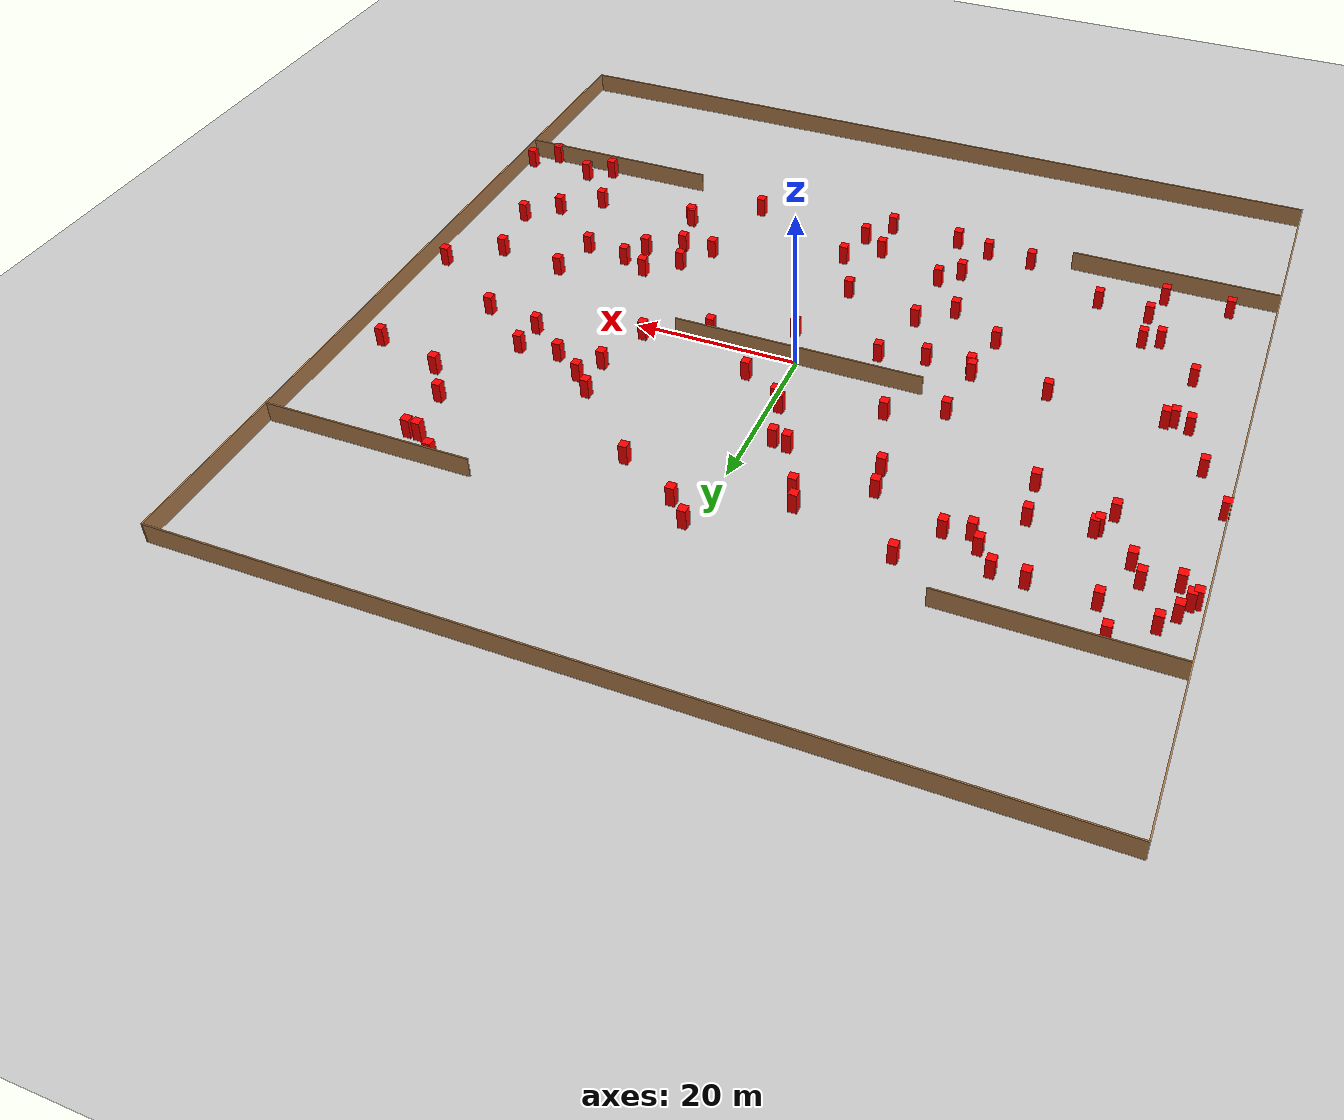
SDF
<sdf version="1.7">
 <world name="default">
  <light name="sun" type="directional">
   <pose>0 0 10 0 -0 0</pose>
   <diffuse>0.8 0.8 0.8 1</diffuse>
   <specular>0.2 0.2 0.2 1</specular>
   <attenuation>
    <range>1000</range>
    <constant>0.9</constant>
    <linear>0.01</linear>
    <quadratic>0.001</quadratic>
   </attenuation>
   <direction>-0.5 0.1 -0.9</direction>
   <spot><inner_angle>0</inner_angle><outer_angle>0</outer_angle><falloff>0</falloff></spot>
  </light>
  <model name="ground_plane">
   <static>1</static>
   <link name="link">
    <collision name="collision">
     <geometry><plane><normal>0 0 1</normal><size>100 100</size></plane></geometry>
     <surface>
      <contact><collide_bitmask>65535</collide_bitmask></contact>
      <friction><ode><mu>100</mu><mu2>50</mu2></ode></friction>
     </surface>
    </collision>
    <visual name="visual">
     <cast_shadows>0</cast_shadows>
     <geometry><plane><normal>0 0 1</normal><size>100 100</size></plane></geometry>
     <material>
      <script><uri>file://media/materials/scripts/gazebo.material</uri><name>Gazebo/Grey</name></script>
     </material>
    </visual>
   </link>
  </model>
  <gravity>0 0 -9.8</gravity>
  <magnetic_field>6e-06 2.3e-05 -4.2e-05</magnetic_field>
  <atmosphere type="adiabatic"/>
  <physics type="ode">
   <max_step_size>0.001</max_step_size>
   <real_time_factor>1</real_time_factor>
   <real_time_update_rate>1000</real_time_update_rate>
  </physics>
  <scene><ambient>0.4 0.4 0.4 1</ambient><background>0.7 0.7 0.7 1</background><shadows>1</shadows></scene>
  <spherical_coordinates>
   <surface_model>EARTH_WGS84</surface_model>
   <latitude_deg>0</latitude_deg>
   <longitude_deg>0</longitude_deg>
   <elevation>0</elevation>
   <heading_deg>0</heading_deg>
  </spherical_coordinates>
  <model name="my_base_walls">
   <link name="Wall_0">
    <collision name="Wall_0_Collision">
     <geometry><box><size>100.15 0.15 2.5</size></box></geometry>
     <pose>0 0 1.25 0 -0 0</pose>
    </collision>
    <visual name="Wall_0_Visual">
     <pose>0 0 1.25 0 -0 0</pose>
     <geometry><box><size>100.15 0.15 2.5</size></box></geometry>
     <material>
      <script><uri>file://media/materials/scripts/gazebo.material</uri><name>Gazebo/Wood</name></script>
      <ambient>1 1 1 1</ambient>
     </material>
     <meta><layer>0</layer></meta>
    </visual>
    <pose>0 -50 0 0 -0 0</pose>
   </link>
   <link name="Wall_10">
    <collision name="Wall_10_Collision">
     <geometry><box><size>25.15 0.15 2.5</size></box></geometry>
     <pose>0 0 1.25 0 -0 0</pose>
    </collision>
    <visual name="Wall_10_Visual">
     <pose>0 0 1.25 0 -0 0</pose>
     <geometry><box><size>25.15 0.15 2.5</size></box></geometry>
     <material>
      <script><uri>file://media/materials/scripts/gazebo.material</uri><name>Gazebo/Wood</name></script>
      <ambient>1 1 1 1</ambient>
     </material>
     <meta><layer>0</layer></meta>
    </visual>
    <pose>37.5 30 0 0 -0 0</pose>
   </link>
   <link name="Wall_12">
    <collision name="Wall_12_Collision">
     <geometry><box><size>25.15 0.15 2.5</size></box></geometry>
     <pose>0 0 1.25 0 -0 0</pose>
    </collision>
    <visual name="Wall_12_Visual">
     <pose>0 0 1.25 0 -0 0</pose>
     <geometry><box><size>25.15 0.15 2.5</size></box></geometry>
     <material>
      <script><uri>file://media/materials/scripts/gazebo.material</uri><name>Gazebo/Wood</name></script>
      <ambient>1 1 1 1</ambient>
     </material>
     <meta><layer>0</layer></meta>
    </visual>
    <pose>-37.5 -30 0 0 -0 0</pose>
   </link>
   <link name="Wall_14">
    <collision name="Wall_14_Collision">
     <geometry><box><size>25.15 0.15 2.5</size></box></geometry>
     <pose>0 0 1.25 0 -0 0</pose>
    </collision>
    <visual name="Wall_14_Visual">
     <pose>0 0 1.25 0 -0 0</pose>
     <geometry><box><size>25.15 0.15 2.5</size></box></geometry>
     <material>
      <script><uri>file://media/materials/scripts/gazebo.material</uri><name>Gazebo/Wood</name></script>
      <ambient>1 1 1 1</ambient>
     </material>
     <meta><layer>0</layer></meta>
    </visual>
    <pose>37.5 -30 0 0 -0 0</pose>
   </link>
   <link name="Wall_16">
    <collision name="Wall_16_Collision">
     <geometry><box><size>30.15 0.15 2.5</size></box></geometry>
     <pose>0 0 1.25 0 -0 0</pose>
    </collision>
    <visual name="Wall_16_Visual">
     <pose>0 0 1.25 0 -0 0</pose>
     <geometry><box><size>30.15 0.15 2.5</size></box></geometry>
     <material>
      <script><uri>file://media/materials/scripts/gazebo.material</uri><name>Gazebo/Wood</name></script>
      <ambient>1 1 1 1</ambient>
     </material>
     <meta><layer>0</layer></meta>
    </visual>
    <pose>0 0 0 0 -0 3.14159</pose>
   </link>
   <link name="Wall_2">
    <collision name="Wall_2_Collision">
     <geometry><box><size>100.15 0.15 2.5</size></box></geometry>
     <pose>0 0 1.25 0 -0 0</pose>
    </collision>
    <visual name="Wall_2_Visual">
     <pose>0 0 1.25 0 -0 0</pose>
     <geometry><box><size>100.15 0.15 2.5</size></box></geometry>
     <material>
      <script><uri>file://media/materials/scripts/gazebo.material</uri><name>Gazebo/Wood</name></script>
      <ambient>1 1 1 1</ambient>
     </material>
     <meta><layer>0</layer></meta>
    </visual>
    <pose>0 50 0 0 -0 3.14159</pose>
   </link>
   <link name="Wall_4">
    <collision name="Wall_4_Collision">
     <geometry><box><size>100.15 0.15 2.5</size></box></geometry>
     <pose>0 0 1.25 0 -0 0</pose>
    </collision>
    <visual name="Wall_4_Visual">
     <pose>0 0 1.25 0 -0 0</pose>
     <geometry><box><size>100.15 0.15 2.5</size></box></geometry>
     <material>
      <script><uri>file://media/materials/scripts/gazebo.material</uri><name>Gazebo/Wood</name></script>
      <ambient>1 1 1 1</ambient>
     </material>
     <meta><layer>0</layer></meta>
    </visual>
    <pose>50 0 0 0 -0 -1.5708</pose>
   </link>
   <link name="Wall_6">
    <collision name="Wall_6_Collision">
     <geometry><box><size>100.15 0.15 2.5</size></box></geometry>
     <pose>0 0 1.25 0 -0 0</pose>
    </collision>
    <visual name="Wall_6_Visual">
     <pose>0 0 1.25 0 -0 0</pose>
     <geometry><box><size>100.15 0.15 2.5</size></box></geometry>
     <material>
      <script><uri>file://media/materials/scripts/gazebo.material</uri><name>Gazebo/Wood</name></script>
      <ambient>1 1 1 1</ambient>
     </material>
     <meta><layer>0</layer></meta>
    </visual>
    <pose>-50 0 0 0 -0 1.5708</pose>
   </link>
   <link name="Wall_8">
    <collision name="Wall_8_Collision">
     <geometry><box><size>25.15 0.15 2.5</size></box></geometry>
     <pose>0 0 1.25 0 -0 0</pose>
    </collision>
    <visual name="Wall_8_Visual">
     <pose>0 0 1.25 0 -0 0</pose>
     <geometry><box><size>25.15 0.15 2.5</size></box></geometry>
     <material>
      <script><uri>file://media/materials/scripts/gazebo.material</uri><name>Gazebo/Wood</name></script>
      <ambient>1 1 1 1</ambient>
     </material>
     <meta><layer>0</layer></meta>
    </visual>
    <pose>-37.5 30 0 0 -0 0</pose>
   </link>
   <static>1</static>
  </model>
  <model name="box1">
   <static>1</static>
   <link name="link">
    <inertial>
     <mass>1</mass>
     <inertia><ixx>0.083</ixx><ixy>0</ixy><ixz>0</ixz><iyy>0.083</iyy><iyz>0</iyz><izz>0.083</izz></inertia>
    </inertial>
    <collision name="collision"><geometry><box><size>1 1 2.5</size></box></geometry></collision>
    <visual name="visual">
     <geometry><box><size>1 1 2.5</size></box></geometry>
     <material>
      <ambient>1 0 0 1</ambient>
      <diffuse>1 0 0 1</diffuse>
      <specular>0.1 0.1 0.1 1</specular>
      <emissive>0 0 0 0</emissive>
     </material>
    </visual>
   </link>
   <pose>-49.0814 20.8101 1.25 0 -0 0</pose>
  </model>
  <model name="box2">
   <static>1</static>
   <link name="link">
    <inertial>
     <mass>1</mass>
     <inertia><ixx>0.083</ixx><ixy>0</ixy><ixz>0</ixz><iyy>0.083</iyy><iyz>0</iyz><izz>0.083</izz></inertia>
    </inertial>
    <collision name="collision"><geometry><box><size>1 1 2.5</size></box></geometry></collision>
    <visual name="visual">
     <geometry><box><size>1 1 2.5</size></box></geometry>
     <material>
      <ambient>1 0 0 1</ambient>
      <diffuse>1 0 0 1</diffuse>
      <specular>0.1 0.1 0.1 1</specular>
      <emissive>0 0 0 0</emissive>
     </material>
    </visual>
   </link>
   <pose>-41.8557 28.1957 1.25 0 -0 0</pose>
  </model>
  <model name="box3">
   <static>1</static>
   <link name="link">
    <inertial>
     <mass>1</mass>
     <inertia><ixx>0.083</ixx><ixy>0</ixy><ixz>0</ixz><iyy>0.083</iyy><iyz>0</iyz><izz>0.083</izz></inertia>
    </inertial>
    <collision name="collision"><geometry><box><size>1 1 2.5</size></box></geometry></collision>
    <visual name="visual">
     <geometry><box><size>1 1 2.5</size></box></geometry>
     <material>
      <ambient>1 0 0 1</ambient>
      <diffuse>1 0 0 1</diffuse>
      <specular>0.1 0.1 0.1 1</specular>
      <emissive>0 0 0 0</emissive>
     </material>
    </visual>
   </link>
   <pose>23.1763 -22.4759 1.25 0 -0 0</pose>
  </model>
  <model name="box4">
   <static>1</static>
   <link name="link">
    <inertial>
     <mass>1</mass>
     <inertia><ixx>0.083</ixx><ixy>0</ixy><ixz>0</ixz><iyy>0.083</iyy><iyz>0</iyz><izz>0.083</izz></inertia>
    </inertial>
    <collision name="collision"><geometry><box><size>1 1 2.5</size></box></geometry></collision>
    <visual name="visual">
     <geometry><box><size>1 1 2.5</size></box></geometry>
     <material>
      <ambient>1 0 0 1</ambient>
      <diffuse>1 0 0 1</diffuse>
      <specular>0.1 0.1 0.1 1</specular>
      <emissive>0 0 0 0</emissive>
     </material>
    </visual>
   </link>
   <pose>-20.4027 -11.4088 1.25 0 -0 0</pose>
  </model>
  <model name="box5">
   <static>1</static>
   <link name="link">
    <inertial>
     <mass>1</mass>
     <inertia><ixx>0.083</ixx><ixy>0</ixy><ixz>0</ixz><iyy>0.083</iyy><iyz>0</iyz><izz>0.083</izz></inertia>
    </inertial>
    <collision name="collision"><geometry><box><size>1 1 2.5</size></box></geometry></collision>
    <visual name="visual">
     <geometry><box><size>1 1 2.5</size></box></geometry>
     <material>
      <ambient>1 0 0 1</ambient>
      <diffuse>1 0 0 1</diffuse>
      <specular>0.1 0.1 0.1 1</specular>
      <emissive>0 0 0 0</emissive>
     </material>
    </visual>
   </link>
   <pose>25.5556 -14.0156 1.25 0 -0 0</pose>
  </model>
  <model name="box6">
   <static>1</static>
   <link name="link">
    <inertial>
     <mass>1</mass>
     <inertia><ixx>0.083</ixx><ixy>0</ixy><ixz>0</ixz><iyy>0.083</iyy><iyz>0</iyz><izz>0.083</izz></inertia>
    </inertial>
    <collision name="collision"><geometry><box><size>1 1 2.5</size></box></geometry></collision>
    <visual name="visual">
     <geometry><box><size>1 1 2.5</size></box></geometry>
     <material>
      <ambient>1 0 0 1</ambient>
      <diffuse>1 0 0 1</diffuse>
      <specular>0.1 0.1 0.1 1</specular>
      <emissive>0 0 0 0</emissive>
     </material>
    </visual>
   </link>
   <pose>10.8495 21.9933 1.25 0 -0 0</pose>
  </model>
  <model name="box7">
   <static>1</static>
   <link name="link">
    <inertial>
     <mass>1</mass>
     <inertia><ixx>0.083</ixx><ixy>0</ixy><ixz>0</ixz><iyy>0.083</iyy><iyz>0</iyz><izz>0.083</izz></inertia>
    </inertial>
    <collision name="collision"><geometry><box><size>1 1 2.5</size></box></geometry></collision>
    <visual name="visual">
     <geometry><box><size>1 1 2.5</size></box></geometry>
     <material>
      <ambient>1 0 0 1</ambient>
      <diffuse>1 0 0 1</diffuse>
      <specular>0.1 0.1 0.1 1</specular>
      <emissive>0 0 0 0</emissive>
     </material>
    </visual>
   </link>
   <pose>-40.265 24.2819 1.25 0 -0 0</pose>
  </model>
  <model name="box8">
   <static>1</static>
   <link name="link">
    <inertial>
     <mass>1</mass>
     <inertia><ixx>0.083</ixx><ixy>0</ixy><ixz>0</ixz><iyy>0.083</iyy><iyz>0</iyz><izz>0.083</izz></inertia>
    </inertial>
    <collision name="collision"><geometry><box><size>1 1 2.5</size></box></geometry></collision>
    <visual name="visual">
     <geometry><box><size>1 1 2.5</size></box></geometry>
     <material>
      <ambient>1 0 0 1</ambient>
      <diffuse>1 0 0 1</diffuse>
      <specular>0.1 0.1 0.1 1</specular>
      <emissive>0 0 0 0</emissive>
     </material>
    </visual>
   </link>
   <pose>2.00673 -4.99949 1.25 0 -0 0</pose>
  </model>
  <model name="box9">
   <static>1</static>
   <link name="link">
    <inertial>
     <mass>1</mass>
     <inertia><ixx>0.083</ixx><ixy>0</ixy><ixz>0</ixz><iyy>0.083</iyy><iyz>0</iyz><izz>0.083</izz></inertia>
    </inertial>
    <collision name="collision"><geometry><box><size>1 1 2.5</size></box></geometry></collision>
    <visual name="visual">
     <geometry><box><size>1 1 2.5</size></box></geometry>
     <material>
      <ambient>1 0 0 1</ambient>
      <diffuse>1 0 0 1</diffuse>
      <specular>0.1 0.1 0.1 1</specular>
      <emissive>0 0 0 0</emissive>
     </material>
    </visual>
   </link>
   <pose>20.3451 8.47321 1.25 0 -0 0</pose>
  </model>
  <model name="box10">
   <static>1</static>
   <link name="link">
    <inertial>
     <mass>1</mass>
     <inertia><ixx>0.083</ixx><ixy>0</ixy><ixz>0</ixz><iyy>0.083</iyy><iyz>0</iyz><izz>0.083</izz></inertia>
    </inertial>
    <collision name="collision"><geometry><box><size>1 1 2.5</size></box></geometry></collision>
    <visual name="visual">
     <geometry><box><size>1 1 2.5</size></box></geometry>
     <material>
      <ambient>1 0 0 1</ambient>
      <diffuse>1 0 0 1</diffuse>
      <specular>0.1 0.1 0.1 1</specular>
      <emissive>0 0 0 0</emissive>
     </material>
    </visual>
   </link>
   <pose>-47.2471 19.1602 1.25 0 -0 0</pose>
  </model>
  <model name="box11">
   <static>1</static>
   <link name="link">
    <inertial>
     <mass>1</mass>
     <inertia><ixx>0.083</ixx><ixy>0</ixy><ixz>0</ixz><iyy>0.083</iyy><iyz>0</iyz><izz>0.083</izz></inertia>
    </inertial>
    <collision name="collision"><geometry><box><size>1 1 2.5</size></box></geometry></collision>
    <visual name="visual">
     <geometry><box><size>1 1 2.5</size></box></geometry>
     <material>
      <ambient>1 0 0 1</ambient>
      <diffuse>1 0 0 1</diffuse>
      <specular>0.1 0.1 0.1 1</specular>
      <emissive>0 0 0 0</emissive>
     </material>
    </visual>
   </link>
   <pose>-10.4361 -29.6285 1.25 0 -0 0</pose>
  </model>
  <model name="box12">
   <static>1</static>
   <link name="link">
    <inertial>
     <mass>1</mass>
     <inertia><ixx>0.083</ixx><ixy>0</ixy><ixz>0</ixz><iyy>0.083</iyy><iyz>0</iyz><izz>0.083</izz></inertia>
    </inertial>
    <collision name="collision"><geometry><box><size>1 1 2.5</size></box></geometry></collision>
    <visual name="visual">
     <geometry><box><size>1 1 2.5</size></box></geometry>
     <material>
      <ambient>1 0 0 1</ambient>
      <diffuse>1 0 0 1</diffuse>
      <specular>0.1 0.1 0.1 1</specular>
      <emissive>0 0 0 0</emissive>
     </material>
    </visual>
   </link>
   <pose>-49.6268 7.5907 1.25 0 -0 0</pose>
  </model>
  <model name="box13">
   <static>1</static>
   <link name="link">
    <inertial>
     <mass>1</mass>
     <inertia><ixx>0.083</ixx><ixy>0</ixy><ixz>0</ixz><iyy>0.083</iyy><iyz>0</iyz><izz>0.083</izz></inertia>
    </inertial>
    <collision name="collision"><geometry><box><size>1 1 2.5</size></box></geometry></collision>
    <visual name="visual">
     <geometry><box><size>1 1 2.5</size></box></geometry>
     <material>
      <ambient>1 0 0 1</ambient>
      <diffuse>1 0 0 1</diffuse>
      <specular>0.1 0.1 0.1 1</specular>
      <emissive>0 0 0 0</emissive>
     </material>
    </visual>
   </link>
   <pose>-33.1486 24.1292 1.25 0 -0 0</pose>
  </model>
  <model name="box14">
   <static>1</static>
   <link name="link">
    <inertial>
     <mass>1</mass>
     <inertia><ixx>0.083</ixx><ixy>0</ixy><ixz>0</ixz><iyy>0.083</iyy><iyz>0</iyz><izz>0.083</izz></inertia>
    </inertial>
    <collision name="collision"><geometry><box><size>1 1 2.5</size></box></geometry></collision>
    <visual name="visual">
     <geometry><box><size>1 1 2.5</size></box></geometry>
     <material>
      <ambient>1 0 0 1</ambient>
      <diffuse>1 0 0 1</diffuse>
      <specular>0.1 0.1 0.1 1</specular>
      <emissive>0 0 0 0</emissive>
     </material>
    </visual>
   </link>
   <pose>37.737 -28.9766 1.25 0 -0 0</pose>
  </model>
  <model name="box15">
   <static>1</static>
   <link name="link">
    <inertial>
     <mass>1</mass>
     <inertia><ixx>0.083</ixx><ixy>0</ixy><ixz>0</ixz><iyy>0.083</iyy><iyz>0</iyz><izz>0.083</izz></inertia>
    </inertial>
    <collision name="collision"><geometry><box><size>1 1 2.5</size></box></geometry></collision>
    <visual name="visual">
     <geometry><box><size>1 1 2.5</size></box></geometry>
     <material>
      <ambient>1 0 0 1</ambient>
      <diffuse>1 0 0 1</diffuse>
      <specular>0.1 0.1 0.1 1</specular>
      <emissive>0 0 0 0</emissive>
     </material>
    </visual>
   </link>
   <pose>-43.4733 20.1149 1.25 0 -0 0</pose>
  </model>
  <model name="box16">
   <static>1</static>
   <link name="link">
    <inertial>
     <mass>1</mass>
     <inertia><ixx>0.083</ixx><ixy>0</ixy><ixz>0</ixz><iyy>0.083</iyy><iyz>0</iyz><izz>0.083</izz></inertia>
    </inertial>
    <collision name="collision"><geometry><box><size>1 1 2.5</size></box></geometry></collision>
    <visual name="visual">
     <geometry><box><size>1 1 2.5</size></box></geometry>
     <material>
      <ambient>1 0 0 1</ambient>
      <diffuse>1 0 0 1</diffuse>
      <specular>0.1 0.1 0.1 1</specular>
      <emissive>0 0 0 0</emissive>
     </material>
    </visual>
   </link>
   <pose>4.33282 4.29537 1.25 0 -0 0</pose>
  </model>
  <model name="box17">
   <static>1</static>
   <link name="link">
    <inertial>
     <mass>1</mass>
     <inertia><ixx>0.083</ixx><ixy>0</ixy><ixz>0</ixz><iyy>0.083</iyy><iyz>0</iyz><izz>0.083</izz></inertia>
    </inertial>
    <collision name="collision"><geometry><box><size>1 1 2.5</size></box></geometry></collision>
    <visual name="visual">
     <geometry><box><size>1 1 2.5</size></box></geometry>
     <material>
      <ambient>1 0 0 1</ambient>
      <diffuse>1 0 0 1</diffuse>
      <specular>0.1 0.1 0.1 1</specular>
      <emissive>0 0 0 0</emissive>
     </material>
    </visual>
   </link>
   <pose>-14.6766 -28.6023 1.25 0 -0 0</pose>
  </model>
  <model name="box18">
   <static>1</static>
   <link name="link">
    <inertial>
     <mass>1</mass>
     <inertia><ixx>0.083</ixx><ixy>0</ixy><ixz>0</ixz><iyy>0.083</iyy><iyz>0</iyz><izz>0.083</izz></inertia>
    </inertial>
    <collision name="collision"><geometry><box><size>1 1 2.5</size></box></geometry></collision>
    <visual name="visual">
     <geometry><box><size>1 1 2.5</size></box></geometry>
     <material>
      <ambient>1 0 0 1</ambient>
      <diffuse>1 0 0 1</diffuse>
      <specular>0.1 0.1 0.1 1</specular>
      <emissive>0 0 0 0</emissive>
     </material>
    </visual>
   </link>
   <pose>-7.52814 20.1668 1.25 0 -0 0</pose>
  </model>
  <model name="box19">
   <static>1</static>
   <link name="link">
    <inertial>
     <mass>1</mass>
     <inertia><ixx>0.083</ixx><ixy>0</ixy><ixz>0</ixz><iyy>0.083</iyy><iyz>0</iyz><izz>0.083</izz></inertia>
    </inertial>
    <collision name="collision"><geometry><box><size>1 1 2.5</size></box></geometry></collision>
    <visual name="visual">
     <geometry><box><size>1 1 2.5</size></box></geometry>
     <material>
      <ambient>1 0 0 1</ambient>
      <diffuse>1 0 0 1</diffuse>
      <specular>0.1 0.1 0.1 1</specular>
      <emissive>0 0 0 0</emissive>
     </material>
    </visual>
   </link>
   <pose>-20.1599 -28.4555 1.25 0 -0 0</pose>
  </model>
  <model name="box20">
   <static>1</static>
   <link name="link">
    <inertial>
     <mass>1</mass>
     <inertia><ixx>0.083</ixx><ixy>0</ixy><ixz>0</ixz><iyy>0.083</iyy><iyz>0</iyz><izz>0.083</izz></inertia>
    </inertial>
    <collision name="collision"><geometry><box><size>1 1 2.5</size></box></geometry></collision>
    <visual name="visual">
     <geometry><box><size>1 1 2.5</size></box></geometry>
     <material>
      <ambient>1 0 0 1</ambient>
      <diffuse>1 0 0 1</diffuse>
      <specular>0.1 0.1 0.1 1</specular>
      <emissive>0 0 0 0</emissive>
     </material>
    </visual>
   </link>
   <pose>-48.5085 21.2595 1.25 0 -0 0</pose>
  </model>
  <model name="box21">
   <static>1</static>
   <link name="link">
    <inertial>
     <mass>1</mass>
     <inertia><ixx>0.083</ixx><ixy>0</ixy><ixz>0</ixz><iyy>0.083</iyy><iyz>0</iyz><izz>0.083</izz></inertia>
    </inertial>
    <collision name="collision"><geometry><box><size>1 1 2.5</size></box></geometry></collision>
    <visual name="visual">
     <geometry><box><size>1 1 2.5</size></box></geometry>
     <material>
      <ambient>1 0 0 1</ambient>
      <diffuse>1 0 0 1</diffuse>
      <specular>0.1 0.1 0.1 1</specular>
      <emissive>0 0 0 0</emissive>
     </material>
    </visual>
   </link>
   <pose>0.722035 -26.3664 1.25 0 -0 0</pose>
  </model>
  <model name="box22">
   <static>1</static>
   <link name="link">
    <inertial>
     <mass>1</mass>
     <inertia><ixx>0.083</ixx><ixy>0</ixy><ixz>0</ixz><iyy>0.083</iyy><iyz>0</iyz><izz>0.083</izz></inertia>
    </inertial>
    <collision name="collision"><geometry><box><size>1 1 2.5</size></box></geometry></collision>
    <visual name="visual">
     <geometry><box><size>1 1 2.5</size></box></geometry>
     <material>
      <ambient>1 0 0 1</ambient>
      <diffuse>1 0 0 1</diffuse>
      <specular>0.1 0.1 0.1 1</specular>
      <emissive>0 0 0 0</emissive>
     </material>
    </visual>
   </link>
   <pose>-15.5201 17.2574 1.25 0 -0 0</pose>
  </model>
  <model name="box23">
   <static>1</static>
   <link name="link">
    <inertial>
     <mass>1</mass>
     <inertia><ixx>0.083</ixx><ixy>0</ixy><ixz>0</ixz><iyy>0.083</iyy><iyz>0</iyz><izz>0.083</izz></inertia>
    </inertial>
    <collision name="collision"><geometry><box><size>1 1 2.5</size></box></geometry></collision>
    <visual name="visual">
     <geometry><box><size>1 1 2.5</size></box></geometry>
     <material>
      <ambient>1 0 0 1</ambient>
      <diffuse>1 0 0 1</diffuse>
      <specular>0.1 0.1 0.1 1</specular>
      <emissive>0 0 0 0</emissive>
     </material>
    </visual>
   </link>
   <pose>-47.6507 23.0816 1.25 0 -0 0</pose>
  </model>
  <model name="box24">
   <static>1</static>
   <link name="link">
    <inertial>
     <mass>1</mass>
     <inertia><ixx>0.083</ixx><ixy>0</ixy><ixz>0</ixz><iyy>0.083</iyy><iyz>0</iyz><izz>0.083</izz></inertia>
    </inertial>
    <collision name="collision"><geometry><box><size>1 1 2.5</size></box></geometry></collision>
    <visual name="visual">
     <geometry><box><size>1 1 2.5</size></box></geometry>
     <material>
      <ambient>1 0 0 1</ambient>
      <diffuse>1 0 0 1</diffuse>
      <specular>0.1 0.1 0.1 1</specular>
      <emissive>0 0 0 0</emissive>
     </material>
    </visual>
   </link>
   <pose>-18.6832 2.72705 1.25 0 -0 0</pose>
  </model>
  <model name="box25">
   <static>1</static>
   <link name="link">
    <inertial>
     <mass>1</mass>
     <inertia><ixx>0.083</ixx><ixy>0</ixy><ixz>0</ixz><iyy>0.083</iyy><iyz>0</iyz><izz>0.083</izz></inertia>
    </inertial>
    <collision name="collision"><geometry><box><size>1 1 2.5</size></box></geometry></collision>
    <visual name="visual">
     <geometry><box><size>1 1 2.5</size></box></geometry>
     <material>
      <ambient>1 0 0 1</ambient>
      <diffuse>1 0 0 1</diffuse>
      <specular>0.1 0.1 0.1 1</specular>
      <emissive>0 0 0 0</emissive>
     </material>
    </visual>
   </link>
   <pose>40.6324 -27.2331 1.25 0 -0 0</pose>
  </model>
  <model name="box26">
   <static>1</static>
   <link name="link">
    <inertial>
     <mass>1</mass>
     <inertia><ixx>0.083</ixx><ixy>0</ixy><ixz>0</ixz><iyy>0.083</iyy><iyz>0</iyz><izz>0.083</izz></inertia>
    </inertial>
    <collision name="collision"><geometry><box><size>1 1 2.5</size></box></geometry></collision>
    <visual name="visual">
     <geometry><box><size>1 1 2.5</size></box></geometry>
     <material>
      <ambient>1 0 0 1</ambient>
      <diffuse>1 0 0 1</diffuse>
      <specular>0.1 0.1 0.1 1</specular>
      <emissive>0 0 0 0</emissive>
     </material>
    </visual>
   </link>
   <pose>43.5856 -15.3946 1.25 0 -0 0</pose>
  </model>
  <model name="box27">
   <static>1</static>
   <link name="link">
    <inertial>
     <mass>1</mass>
     <inertia><ixx>0.083</ixx><ixy>0</ixy><ixz>0</ixz><iyy>0.083</iyy><iyz>0</iyz><izz>0.083</izz></inertia>
    </inertial>
    <collision name="collision"><geometry><box><size>1 1 2.5</size></box></geometry></collision>
    <visual name="visual">
     <geometry><box><size>1 1 2.5</size></box></geometry>
     <material>
      <ambient>1 0 0 1</ambient>
      <diffuse>1 0 0 1</diffuse>
      <specular>0.1 0.1 0.1 1</specular>
      <emissive>0 0 0 0</emissive>
     </material>
    </visual>
   </link>
   <pose>-15.0135 13.8962 1.25 0 -0 0</pose>
  </model>
  <model name="box28">
   <static>1</static>
   <link name="link">
    <inertial>
     <mass>1</mass>
     <inertia><ixx>0.083</ixx><ixy>0</ixy><ixz>0</ixz><iyy>0.083</iyy><iyz>0</iyz><izz>0.083</izz></inertia>
    </inertial>
    <collision name="collision"><geometry><box><size>1 1 2.5</size></box></geometry></collision>
    <visual name="visual">
     <geometry><box><size>1 1 2.5</size></box></geometry>
     <material>
      <ambient>1 0 0 1</ambient>
      <diffuse>1 0 0 1</diffuse>
      <specular>0.1 0.1 0.1 1</specular>
      <emissive>0 0 0 0</emissive>
     </material>
    </visual>
   </link>
   <pose>49.0233 -27.6356 1.25 0 -0 0</pose>
  </model>
  <model name="box29">
   <static>1</static>
   <link name="link">
    <inertial>
     <mass>1</mass>
     <inertia><ixx>0.083</ixx><ixy>0</ixy><ixz>0</ixz><iyy>0.083</iyy><iyz>0</iyz><izz>0.083</izz></inertia>
    </inertial>
    <collision name="collision"><geometry><box><size>1 1 2.5</size></box></geometry></collision>
    <visual name="visual">
     <geometry><box><size>1 1 2.5</size></box></geometry>
     <material>
      <ambient>1 0 0 1</ambient>
      <diffuse>1 0 0 1</diffuse>
      <specular>0.1 0.1 0.1 1</specular>
      <emissive>0 0 0 0</emissive>
     </material>
    </visual>
   </link>
   <pose>-46.1264 25.2185 1.25 0 -0 0</pose>
  </model>
  <model name="box30">
   <static>1</static>
   <link name="link">
    <inertial>
     <mass>1</mass>
     <inertia><ixx>0.083</ixx><ixy>0</ixy><ixz>0</ixz><iyy>0.083</iyy><iyz>0</iyz><izz>0.083</izz></inertia>
    </inertial>
    <collision name="collision"><geometry><box><size>1 1 2.5</size></box></geometry></collision>
    <visual name="visual">
     <geometry><box><size>1 1 2.5</size></box></geometry>
     <material>
      <ambient>1 0 0 1</ambient>
      <diffuse>1 0 0 1</diffuse>
      <specular>0.1 0.1 0.1 1</specular>
      <emissive>0 0 0 0</emissive>
     </material>
    </visual>
   </link>
   <pose>30.5931 9.21803 1.25 0 -0 0</pose>
  </model>
  <model name="box31">
   <static>1</static>
   <link name="link">
    <inertial>
     <mass>1</mass>
     <inertia><ixx>0.083</ixx><ixy>0</ixy><ixz>0</ixz><iyy>0.083</iyy><iyz>0</iyz><izz>0.083</izz></inertia>
    </inertial>
    <collision name="collision"><geometry><box><size>1 1 2.5</size></box></geometry></collision>
    <visual name="visual">
     <geometry><box><size>1 1 2.5</size></box></geometry>
     <material>
      <ambient>1 0 0 1</ambient>
      <diffuse>1 0 0 1</diffuse>
      <specular>0.1 0.1 0.1 1</specular>
      <emissive>0 0 0 0</emissive>
     </material>
    </visual>
   </link>
   <pose>-1.77396 -29.8208 1.25 0 -0 0</pose>
  </model>
  <model name="box32">
   <static>1</static>
   <link name="link">
    <inertial>
     <mass>1</mass>
     <inertia><ixx>0.083</ixx><ixy>0</ixy><ixz>0</ixz><iyy>0.083</iyy><iyz>0</iyz><izz>0.083</izz></inertia>
    </inertial>
    <collision name="collision"><geometry><box><size>1 1 2.5</size></box></geometry></collision>
    <visual name="visual">
     <geometry><box><size>1 1 2.5</size></box></geometry>
     <material>
      <ambient>1 0 0 1</ambient>
      <diffuse>1 0 0 1</diffuse>
      <specular>0.1 0.1 0.1 1</specular>
      <emissive>0 0 0 0</emissive>
     </material>
    </visual>
   </link>
   <pose>42.1976 -7.45792 1.25 0 -0 0</pose>
  </model>
  <model name="box33">
   <static>1</static>
   <link name="link">
    <inertial>
     <mass>1</mass>
     <inertia><ixx>0.083</ixx><ixy>0</ixy><ixz>0</ixz><iyy>0.083</iyy><iyz>0</iyz><izz>0.083</izz></inertia>
    </inertial>
    <collision name="collision"><geometry><box><size>1 1 2.5</size></box></geometry></collision>
    <visual name="visual">
     <geometry><box><size>1 1 2.5</size></box></geometry>
     <material>
      <ambient>1 0 0 1</ambient>
      <diffuse>1 0 0 1</diffuse>
      <specular>0.1 0.1 0.1 1</specular>
      <emissive>0 0 0 0</emissive>
     </material>
    </visual>
   </link>
   <pose>-37.787 14.8567 1.25 0 -0 0</pose>
  </model>
  <model name="box34">
   <static>1</static>
   <link name="link">
    <inertial>
     <mass>1</mass>
     <inertia><ixx>0.083</ixx><ixy>0</ixy><ixz>0</ixz><iyy>0.083</iyy><iyz>0</iyz><izz>0.083</izz></inertia>
    </inertial>
    <collision name="collision"><geometry><box><size>1 1 2.5</size></box></geometry></collision>
    <visual name="visual">
     <geometry><box><size>1 1 2.5</size></box></geometry>
     <material>
      <ambient>1 0 0 1</ambient>
      <diffuse>1 0 0 1</diffuse>
      <specular>0.1 0.1 0.1 1</specular>
      <emissive>0 0 0 0</emissive>
     </material>
    </visual>
   </link>
   <pose>-31.0824 15.5782 1.25 0 -0 0</pose>
  </model>
  <model name="box35">
   <static>1</static>
   <link name="link">
    <inertial>
     <mass>1</mass>
     <inertia><ixx>0.083</ixx><ixy>0</ixy><ixz>0</ixz><iyy>0.083</iyy><iyz>0</iyz><izz>0.083</izz></inertia>
    </inertial>
    <collision name="collision"><geometry><box><size>1 1 2.5</size></box></geometry></collision>
    <visual name="visual">
     <geometry><box><size>1 1 2.5</size></box></geometry>
     <material>
      <ambient>1 0 0 1</ambient>
      <diffuse>1 0 0 1</diffuse>
      <specular>0.1 0.1 0.1 1</specular>
      <emissive>0 0 0 0</emissive>
     </material>
    </visual>
   </link>
   <pose>-39.2947 11.8075 1.25 0 -0 0</pose>
  </model>
  <model name="box36">
   <static>1</static>
   <link name="link">
    <inertial>
     <mass>1</mass>
     <inertia><ixx>0.083</ixx><ixy>0</ixy><ixz>0</ixz><iyy>0.083</iyy><iyz>0</iyz><izz>0.083</izz></inertia>
    </inertial>
    <collision name="collision"><geometry><box><size>1 1 2.5</size></box></geometry></collision>
    <visual name="visual">
     <geometry><box><size>1 1 2.5</size></box></geometry>
     <material>
      <ambient>1 0 0 1</ambient>
      <diffuse>1 0 0 1</diffuse>
      <specular>0.1 0.1 0.1 1</specular>
      <emissive>0 0 0 0</emissive>
     </material>
    </visual>
   </link>
   <pose>32.4796 -11.8787 1.25 0 -0 0</pose>
  </model>
  <model name="box37">
   <static>1</static>
   <link name="link">
    <inertial>
     <mass>1</mass>
     <inertia><ixx>0.083</ixx><ixy>0</ixy><ixz>0</ixz><iyy>0.083</iyy><iyz>0</iyz><izz>0.083</izz></inertia>
    </inertial>
    <collision name="collision"><geometry><box><size>1 1 2.5</size></box></geometry></collision>
    <visual name="visual">
     <geometry><box><size>1 1 2.5</size></box></geometry>
     <material>
      <ambient>1 0 0 1</ambient>
      <diffuse>1 0 0 1</diffuse>
      <specular>0.1 0.1 0.1 1</specular>
      <emissive>0 0 0 0</emissive>
     </material>
    </visual>
   </link>
   <pose>34.5388 20.2603 1.25 0 -0 0</pose>
  </model>
  <model name="box38">
   <static>1</static>
   <link name="link">
    <inertial>
     <mass>1</mass>
     <inertia><ixx>0.083</ixx><ixy>0</ixy><ixz>0</ixz><iyy>0.083</iyy><iyz>0</iyz><izz>0.083</izz></inertia>
    </inertial>
    <collision name="collision"><geometry><box><size>1 1 2.5</size></box></geometry></collision>
    <visual name="visual">
     <geometry><box><size>1 1 2.5</size></box></geometry>
     <material>
      <ambient>1 0 0 1</ambient>
      <diffuse>1 0 0 1</diffuse>
      <specular>0.1 0.1 0.1 1</specular>
      <emissive>0 0 0 0</emissive>
     </material>
    </visual>
   </link>
   <pose>46.287 -29.8516 1.25 0 -0 0</pose>
  </model>
  <model name="box39">
   <static>1</static>
   <link name="link">
    <inertial>
     <mass>1</mass>
     <inertia><ixx>0.083</ixx><ixy>0</ixy><ixz>0</ixz><iyy>0.083</iyy><iyz>0</iyz><izz>0.083</izz></inertia>
    </inertial>
    <collision name="collision"><geometry><box><size>1 1 2.5</size></box></geometry></collision>
    <visual name="visual">
     <geometry><box><size>1 1 2.5</size></box></geometry>
     <material>
      <ambient>1 0 0 1</ambient>
      <diffuse>1 0 0 1</diffuse>
      <specular>0.1 0.1 0.1 1</specular>
      <emissive>0 0 0 0</emissive>
     </material>
    </visual>
   </link>
   <pose>-29.7186 -23.4482 1.25 0 -0 0</pose>
  </model>
  <model name="box40">
   <static>1</static>
   <link name="link">
    <inertial>
     <mass>1</mass>
     <inertia><ixx>0.083</ixx><ixy>0</ixy><ixz>0</ixz><iyy>0.083</iyy><iyz>0</iyz><izz>0.083</izz></inertia>
    </inertial>
    <collision name="collision"><geometry><box><size>1 1 2.5</size></box></geometry></collision>
    <visual name="visual">
     <geometry><box><size>1 1 2.5</size></box></geometry>
     <material>
      <ambient>1 0 0 1</ambient>
      <diffuse>1 0 0 1</diffuse>
      <specular>0.1 0.1 0.1 1</specular>
      <emissive>0 0 0 0</emissive>
     </material>
    </visual>
   </link>
   <pose>37.5108 3.95148 1.25 0 -0 0</pose>
  </model>
  <model name="box41">
   <static>1</static>
   <link name="link">
    <inertial>
     <mass>1</mass>
     <inertia><ixx>0.083</ixx><ixy>0</ixy><ixz>0</ixz><iyy>0.083</iyy><iyz>0</iyz><izz>0.083</izz></inertia>
    </inertial>
    <collision name="collision"><geometry><box><size>1 1 2.5</size></box></geometry></collision>
    <visual name="visual">
     <geometry><box><size>1 1 2.5</size></box></geometry>
     <material>
      <ambient>1 0 0 1</ambient>
      <diffuse>1 0 0 1</diffuse>
      <specular>0.1 0.1 0.1 1</specular>
      <emissive>0 0 0 0</emissive>
     </material>
    </visual>
   </link>
   <pose>-29.6103 23.9536 1.25 0 -0 0</pose>
  </model>
  <model name="box42">
   <static>1</static>
   <link name="link">
    <inertial>
     <mass>1</mass>
     <inertia><ixx>0.083</ixx><ixy>0</ixy><ixz>0</ixz><iyy>0.083</iyy><iyz>0</iyz><izz>0.083</izz></inertia>
    </inertial>
    <collision name="collision"><geometry><box><size>1 1 2.5</size></box></geometry></collision>
    <visual name="visual">
     <geometry><box><size>1 1 2.5</size></box></geometry>
     <material>
      <ambient>1 0 0 1</ambient>
      <diffuse>1 0 0 1</diffuse>
      <specular>0.1 0.1 0.1 1</specular>
      <emissive>0 0 0 0</emissive>
     </material>
    </visual>
   </link>
   <pose>-30.6275 10.3452 1.25 0 -0 0</pose>
  </model>
  <model name="box43">
   <static>1</static>
   <link name="link">
    <inertial>
     <mass>1</mass>
     <inertia><ixx>0.083</ixx><ixy>0</ixy><ixz>0</ixz><iyy>0.083</iyy><iyz>0</iyz><izz>0.083</izz></inertia>
    </inertial>
    <collision name="collision"><geometry><box><size>1 1 2.5</size></box></geometry></collision>
    <visual name="visual">
     <geometry><box><size>1 1 2.5</size></box></geometry>
     <material>
      <ambient>1 0 0 1</ambient>
      <diffuse>1 0 0 1</diffuse>
      <specular>0.1 0.1 0.1 1</specular>
      <emissive>0 0 0 0</emissive>
     </material>
    </visual>
   </link>
   <pose>-20.1712 25.5491 1.25 0 -0 0</pose>
  </model>
  <model name="box44">
   <static>1</static>
   <link name="link">
    <inertial>
     <mass>1</mass>
     <inertia><ixx>0.083</ixx><ixy>0</ixy><ixz>0</ixz><iyy>0.083</iyy><iyz>0</iyz><izz>0.083</izz></inertia>
    </inertial>
    <collision name="collision"><geometry><box><size>1 1 2.5</size></box></geometry></collision>
    <visual name="visual">
     <geometry><box><size>1 1 2.5</size></box></geometry>
     <material>
      <ambient>1 0 0 1</ambient>
      <diffuse>1 0 0 1</diffuse>
      <specular>0.1 0.1 0.1 1</specular>
      <emissive>0 0 0 0</emissive>
     </material>
    </visual>
   </link>
   <pose>-2.79529 13.8154 1.25 0 -0 0</pose>
  </model>
  <model name="box45">
   <static>1</static>
   <link name="link">
    <inertial>
     <mass>1</mass>
     <inertia><ixx>0.083</ixx><ixy>0</ixy><ixz>0</ixz><iyy>0.083</iyy><iyz>0</iyz><izz>0.083</izz></inertia>
    </inertial>
    <collision name="collision"><geometry><box><size>1 1 2.5</size></box></geometry></collision>
    <visual name="visual">
     <geometry><box><size>1 1 2.5</size></box></geometry>
     <material>
      <ambient>1 0 0 1</ambient>
      <diffuse>1 0 0 1</diffuse>
      <specular>0.1 0.1 0.1 1</specular>
      <emissive>0 0 0 0</emissive>
     </material>
    </visual>
   </link>
   <pose>11.3143 -1.65347 1.25 0 -0 0</pose>
  </model>
  <model name="box46">
   <static>1</static>
   <link name="link">
    <inertial>
     <mass>1</mass>
     <inertia><ixx>0.083</ixx><ixy>0</ixy><ixz>0</ixz><iyy>0.083</iyy><iyz>0</iyz><izz>0.083</izz></inertia>
    </inertial>
    <collision name="collision"><geometry><box><size>1 1 2.5</size></box></geometry></collision>
    <visual name="visual">
     <geometry><box><size>1 1 2.5</size></box></geometry>
     <material>
      <ambient>1 0 0 1</ambient>
      <diffuse>1 0 0 1</diffuse>
      <specular>0.1 0.1 0.1 1</specular>
      <emissive>0 0 0 0</emissive>
     </material>
    </visual>
   </link>
   <pose>-26.5055 19.658 1.25 0 -0 0</pose>
  </model>
  <model name="box47">
   <static>1</static>
   <link name="link">
    <inertial>
     <mass>1</mass>
     <inertia><ixx>0.083</ixx><ixy>0</ixy><ixz>0</ixz><iyy>0.083</iyy><iyz>0</iyz><izz>0.083</izz></inertia>
    </inertial>
    <collision name="collision"><geometry><box><size>1 1 2.5</size></box></geometry></collision>
    <visual name="visual">
     <geometry><box><size>1 1 2.5</size></box></geometry>
     <material>
      <ambient>1 0 0 1</ambient>
      <diffuse>1 0 0 1</diffuse>
      <specular>0.1 0.1 0.1 1</specular>
      <emissive>0 0 0 0</emissive>
     </material>
    </visual>
   </link>
   <pose>-13.8101 -5.54181 1.25 0 -0 0</pose>
  </model>
  <model name="box48">
   <static>1</static>
   <link name="link">
    <inertial>
     <mass>1</mass>
     <inertia><ixx>0.083</ixx><ixy>0</ixy><ixz>0</ixz><iyy>0.083</iyy><iyz>0</iyz><izz>0.083</izz></inertia>
    </inertial>
    <collision name="collision"><geometry><box><size>1 1 2.5</size></box></geometry></collision>
    <visual name="visual">
     <geometry><box><size>1 1 2.5</size></box></geometry>
     <material>
      <ambient>1 0 0 1</ambient>
      <diffuse>1 0 0 1</diffuse>
      <specular>0.1 0.1 0.1 1</specular>
      <emissive>0 0 0 0</emissive>
     </material>
    </visual>
   </link>
   <pose>1.04427 28.5568 1.25 0 -0 0</pose>
  </model>
  <model name="box49">
   <static>1</static>
   <link name="link">
    <inertial>
     <mass>1</mass>
     <inertia><ixx>0.083</ixx><ixy>0</ixy><ixz>0</ixz><iyy>0.083</iyy><iyz>0</iyz><izz>0.083</izz></inertia>
    </inertial>
    <collision name="collision"><geometry><box><size>1 1 2.5</size></box></geometry></collision>
    <visual name="visual">
     <geometry><box><size>1 1 2.5</size></box></geometry>
     <material>
      <ambient>1 0 0 1</ambient>
      <diffuse>1 0 0 1</diffuse>
      <specular>0.1 0.1 0.1 1</specular>
      <emissive>0 0 0 0</emissive>
     </material>
    </visual>
   </link>
   <pose>-35.9334 -22.6368 1.25 0 -0 0</pose>
  </model>
  <model name="box50">
   <static>1</static>
   <link name="link">
    <inertial>
     <mass>1</mass>
     <inertia><ixx>0.083</ixx><ixy>0</ixy><ixz>0</ixz><iyy>0.083</iyy><iyz>0</iyz><izz>0.083</izz></inertia>
    </inertial>
    <collision name="collision"><geometry><box><size>1 1 2.5</size></box></geometry></collision>
    <visual name="visual">
     <geometry><box><size>1 1 2.5</size></box></geometry>
     <material>
      <ambient>1 0 0 1</ambient>
      <diffuse>1 0 0 1</diffuse>
      <specular>0.1 0.1 0.1 1</specular>
      <emissive>0 0 0 0</emissive>
     </material>
    </visual>
   </link>
   <pose>15.4877 -27.624 1.25 0 -0 0</pose>
  </model>
  <model name="box51">
   <static>1</static>
   <link name="link">
    <inertial>
     <mass>1</mass>
     <inertia><ixx>0.083</ixx><ixy>0</ixy><ixz>0</ixz><iyy>0.083</iyy><iyz>0</iyz><izz>0.083</izz></inertia>
    </inertial>
    <collision name="collision"><geometry><box><size>1 1 2.5</size></box></geometry></collision>
    <visual name="visual">
     <geometry><box><size>1 1 2.5</size></box></geometry>
     <material>
      <ambient>1 0 0 1</ambient>
      <diffuse>1 0 0 1</diffuse>
      <specular>0.1 0.1 0.1 1</specular>
      <emissive>0 0 0 0</emissive>
     </material>
    </visual>
   </link>
   <pose>-38.1168 -18.4145 1.25 0 -0 0</pose>
  </model>
  <model name="box52">
   <static>1</static>
   <link name="link">
    <inertial>
     <mass>1</mass>
     <inertia><ixx>0.083</ixx><ixy>0</ixy><ixz>0</ixz><iyy>0.083</iyy><iyz>0</iyz><izz>0.083</izz></inertia>
    </inertial>
    <collision name="collision"><geometry><box><size>1 1 2.5</size></box></geometry></collision>
    <visual name="visual">
     <geometry><box><size>1 1 2.5</size></box></geometry>
     <material>
      <ambient>1 0 0 1</ambient>
      <diffuse>1 0 0 1</diffuse>
      <specular>0.1 0.1 0.1 1</specular>
      <emissive>0 0 0 0</emissive>
     </material>
    </visual>
   </link>
   <pose>-1.30681 8.3452 1.25 0 -0 0</pose>
  </model>
  <model name="box53">
   <static>1</static>
   <link name="link">
    <inertial>
     <mass>1</mass>
     <inertia><ixx>0.083</ixx><ixy>0</ixy><ixz>0</ixz><iyy>0.083</iyy><iyz>0</iyz><izz>0.083</izz></inertia>
    </inertial>
    <collision name="collision"><geometry><box><size>1 1 2.5</size></box></geometry></collision>
    <visual name="visual">
     <geometry><box><size>1 1 2.5</size></box></geometry>
     <material>
      <ambient>1 0 0 1</ambient>
      <diffuse>1 0 0 1</diffuse>
      <specular>0.1 0.1 0.1 1</specular>
      <emissive>0 0 0 0</emissive>
     </material>
    </visual>
   </link>
   <pose>30.2579 29.0921 1.25 0 -0 0</pose>
  </model>
  <model name="box54">
   <static>1</static>
   <link name="link">
    <inertial>
     <mass>1</mass>
     <inertia><ixx>0.083</ixx><ixy>0</ixy><ixz>0</ixz><iyy>0.083</iyy><iyz>0</iyz><izz>0.083</izz></inertia>
    </inertial>
    <collision name="collision"><geometry><box><size>1 1 2.5</size></box></geometry></collision>
    <visual name="visual">
     <geometry><box><size>1 1 2.5</size></box></geometry>
     <material>
      <ambient>1 0 0 1</ambient>
      <diffuse>1 0 0 1</diffuse>
      <specular>0.1 0.1 0.1 1</specular>
      <emissive>0 0 0 0</emissive>
     </material>
    </visual>
   </link>
   <pose>-10.3966 -12.0907 1.25 0 -0 0</pose>
  </model>
  <model name="box55">
   <static>1</static>
   <link name="link">
    <inertial>
     <mass>1</mass>
     <inertia><ixx>0.083</ixx><ixy>0</ixy><ixz>0</ixz><iyy>0.083</iyy><iyz>0</iyz><izz>0.083</izz></inertia>
    </inertial>
    <collision name="collision"><geometry><box><size>1 1 2.5</size></box></geometry></collision>
    <visual name="visual">
     <geometry><box><size>1 1 2.5</size></box></geometry>
     <material>
      <ambient>1 0 0 1</ambient>
      <diffuse>1 0 0 1</diffuse>
      <specular>0.1 0.1 0.1 1</specular>
      <emissive>0 0 0 0</emissive>
     </material>
    </visual>
   </link>
   <pose>-19.0479 -5.76204 1.25 0 -0 0</pose>
  </model>
  <model name="box56">
   <static>1</static>
   <link name="link">
    <inertial>
     <mass>1</mass>
     <inertia><ixx>0.083</ixx><ixy>0</ixy><ixz>0</ixz><iyy>0.083</iyy><iyz>0</iyz><izz>0.083</izz></inertia>
    </inertial>
    <collision name="collision"><geometry><box><size>1 1 2.5</size></box></geometry></collision>
    <visual name="visual">
     <geometry><box><size>1 1 2.5</size></box></geometry>
     <material>
      <ambient>1 0 0 1</ambient>
      <diffuse>1 0 0 1</diffuse>
      <specular>0.1 0.1 0.1 1</specular>
      <emissive>0 0 0 0</emissive>
     </material>
    </visual>
   </link>
   <pose>1.83258 -21.2288 1.25 0 -0 0</pose>
  </model>
  <model name="box57">
   <static>1</static>
   <link name="link">
    <inertial>
     <mass>1</mass>
     <inertia><ixx>0.083</ixx><ixy>0</ixy><ixz>0</ixz><iyy>0.083</iyy><iyz>0</iyz><izz>0.083</izz></inertia>
    </inertial>
    <collision name="collision"><geometry><box><size>1 1 2.5</size></box></geometry></collision>
    <visual name="visual">
     <geometry><box><size>1 1 2.5</size></box></geometry>
     <material>
      <ambient>1 0 0 1</ambient>
      <diffuse>1 0 0 1</diffuse>
      <specular>0.1 0.1 0.1 1</specular>
      <emissive>0 0 0 0</emissive>
     </material>
    </visual>
   </link>
   <pose>-28.2291 -4.43584 1.25 0 -0 0</pose>
  </model>
  <model name="box58">
   <static>1</static>
   <link name="link">
    <inertial>
     <mass>1</mass>
     <inertia><ixx>0.083</ixx><ixy>0</ixy><ixz>0</ixz><iyy>0.083</iyy><iyz>0</iyz><izz>0.083</izz></inertia>
    </inertial>
    <collision name="collision"><geometry><box><size>1 1 2.5</size></box></geometry></collision>
    <visual name="visual">
     <geometry><box><size>1 1 2.5</size></box></geometry>
     <material>
      <ambient>1 0 0 1</ambient>
      <diffuse>1 0 0 1</diffuse>
      <specular>0.1 0.1 0.1 1</specular>
      <emissive>0 0 0 0</emissive>
     </material>
    </visual>
   </link>
   <pose>-12.8309 -23.1214 1.25 0 -0 0</pose>
  </model>
  <model name="box59">
   <static>1</static>
   <link name="link">
    <inertial>
     <mass>1</mass>
     <inertia><ixx>0.083</ixx><ixy>0</ixy><ixz>0</ixz><iyy>0.083</iyy><iyz>0</iyz><izz>0.083</izz></inertia>
    </inertial>
    <collision name="collision"><geometry><box><size>1 1 2.5</size></box></geometry></collision>
    <visual name="visual">
     <geometry><box><size>1 1 2.5</size></box></geometry>
     <material>
      <ambient>1 0 0 1</ambient>
      <diffuse>1 0 0 1</diffuse>
      <specular>0.1 0.1 0.1 1</specular>
      <emissive>0 0 0 0</emissive>
     </material>
    </visual>
   </link>
   <pose>27.1607 -11.1651 1.25 0 -0 0</pose>
  </model>
  <model name="box60">
   <static>1</static>
   <link name="link">
    <inertial>
     <mass>1</mass>
     <inertia><ixx>0.083</ixx><ixy>0</ixy><ixz>0</ixz><iyy>0.083</iyy><iyz>0</iyz><izz>0.083</izz></inertia>
    </inertial>
    <collision name="collision"><geometry><box><size>1 1 2.5</size></box></geometry></collision>
    <visual name="visual">
     <geometry><box><size>1 1 2.5</size></box></geometry>
     <material>
      <ambient>1 0 0 1</ambient>
      <diffuse>1 0 0 1</diffuse>
      <specular>0.1 0.1 0.1 1</specular>
      <emissive>0 0 0 0</emissive>
     </material>
    </visual>
   </link>
   <pose>33.1151 26.6832 1.25 0 -0 0</pose>
  </model>
  <model name="box61">
   <static>1</static>
   <link name="link">
    <inertial>
     <mass>1</mass>
     <inertia><ixx>0.083</ixx><ixy>0</ixy><ixz>0</ixz><iyy>0.083</iyy><iyz>0</iyz><izz>0.083</izz></inertia>
    </inertial>
    <collision name="collision"><geometry><box><size>1 1 2.5</size></box></geometry></collision>
    <visual name="visual">
     <geometry><box><size>1 1 2.5</size></box></geometry>
     <material>
      <ambient>1 0 0 1</ambient>
      <diffuse>1 0 0 1</diffuse>
      <specular>0.1 0.1 0.1 1</specular>
      <emissive>0 0 0 0</emissive>
     </material>
    </visual>
   </link>
   <pose>21.4921 -16.3871 1.25 0 -0 0</pose>
  </model>
  <model name="box62">
   <static>1</static>
   <link name="link">
    <inertial>
     <mass>1</mass>
     <inertia><ixx>0.083</ixx><ixy>0</ixy><ixz>0</ixz><iyy>0.083</iyy><iyz>0</iyz><izz>0.083</izz></inertia>
    </inertial>
    <collision name="collision"><geometry><box><size>1 1 2.5</size></box></geometry></collision>
    <visual name="visual">
     <geometry><box><size>1 1 2.5</size></box></geometry>
     <material>
      <ambient>1 0 0 1</ambient>
      <diffuse>1 0 0 1</diffuse>
      <specular>0.1 0.1 0.1 1</specular>
      <emissive>0 0 0 0</emissive>
     </material>
    </visual>
   </link>
   <pose>17.6038 -16.5804 1.25 0 -0 0</pose>
  </model>
  <model name="box63">
   <static>1</static>
   <link name="link">
    <inertial>
     <mass>1</mass>
     <inertia><ixx>0.083</ixx><ixy>0</ixy><ixz>0</ixz><iyy>0.083</iyy><iyz>0</iyz><izz>0.083</izz></inertia>
    </inertial>
    <collision name="collision"><geometry><box><size>1 1 2.5</size></box></geometry></collision>
    <visual name="visual">
     <geometry><box><size>1 1 2.5</size></box></geometry>
     <material>
      <ambient>1 0 0 1</ambient>
      <diffuse>1 0 0 1</diffuse>
      <specular>0.1 0.1 0.1 1</specular>
      <emissive>0 0 0 0</emissive>
     </material>
    </visual>
   </link>
   <pose>30.4641 5.33879 1.25 0 -0 0</pose>
  </model>
  <model name="box64">
   <static>1</static>
   <link name="link">
    <inertial>
     <mass>1</mass>
     <inertia><ixx>0.083</ixx><ixy>0</ixy><ixz>0</ixz><iyy>0.083</iyy><iyz>0</iyz><izz>0.083</izz></inertia>
    </inertial>
    <collision name="collision"><geometry><box><size>1 1 2.5</size></box></geometry></collision>
    <visual name="visual">
     <geometry><box><size>1 1 2.5</size></box></geometry>
     <material>
      <ambient>1 0 0 1</ambient>
      <diffuse>1 0 0 1</diffuse>
      <specular>0.1 0.1 0.1 1</specular>
      <emissive>0 0 0 0</emissive>
     </material>
    </visual>
   </link>
   <pose>-12.3783 5.24012 1.25 0 -0 0</pose>
  </model>
  <model name="box65">
   <static>1</static>
   <link name="link">
    <inertial>
     <mass>1</mass>
     <inertia><ixx>0.083</ixx><ixy>0</ixy><ixz>0</ixz><iyy>0.083</iyy><iyz>0</iyz><izz>0.083</izz></inertia>
    </inertial>
    <collision name="collision"><geometry><box><size>1 1 2.5</size></box></geometry></collision>
    <visual name="visual">
     <geometry><box><size>1 1 2.5</size></box></geometry>
     <material>
      <ambient>1 0 0 1</ambient>
      <diffuse>1 0 0 1</diffuse>
      <specular>0.1 0.1 0.1 1</specular>
      <emissive>0 0 0 0</emissive>
     </material>
    </visual>
   </link>
   <pose>3.54281 25.9941 1.25 0 -0 0</pose>
  </model>
  <model name="box66">
   <static>1</static>
   <link name="link">
    <inertial>
     <mass>1</mass>
     <inertia><ixx>0.083</ixx><ixy>0</ixy><ixz>0</ixz><iyy>0.083</iyy><iyz>0</iyz><izz>0.083</izz></inertia>
    </inertial>
    <collision name="collision"><geometry><box><size>1 1 2.5</size></box></geometry></collision>
    <visual name="visual">
     <geometry><box><size>1 1 2.5</size></box></geometry>
     <material>
      <ambient>1 0 0 1</ambient>
      <diffuse>1 0 0 1</diffuse>
      <specular>0.1 0.1 0.1 1</specular>
      <emissive>0 0 0 0</emissive>
     </material>
    </visual>
   </link>
   <pose>23.9591 -9.78499 1.25 0 -0 0</pose>
  </model>
  <model name="box67">
   <static>1</static>
   <link name="link">
    <inertial>
     <mass>1</mass>
     <inertia><ixx>0.083</ixx><ixy>0</ixy><ixz>0</ixz><iyy>0.083</iyy><iyz>0</iyz><izz>0.083</izz></inertia>
    </inertial>
    <collision name="collision"><geometry><box><size>1 1 2.5</size></box></geometry></collision>
    <visual name="visual">
     <geometry><box><size>1 1 2.5</size></box></geometry>
     <material>
      <ambient>1 0 0 1</ambient>
      <diffuse>1 0 0 1</diffuse>
      <specular>0.1 0.1 0.1 1</specular>
      <emissive>0 0 0 0</emissive>
     </material>
    </visual>
   </link>
   <pose>-8.47557 22.3762 1.25 0 -0 0</pose>
  </model>
  <model name="box68">
   <static>1</static>
   <link name="link">
    <inertial>
     <mass>1</mass>
     <inertia><ixx>0.083</ixx><ixy>0</ixy><ixz>0</ixz><iyy>0.083</iyy><iyz>0</iyz><izz>0.083</izz></inertia>
    </inertial>
    <collision name="collision"><geometry><box><size>1 1 2.5</size></box></geometry></collision>
    <visual name="visual">
     <geometry><box><size>1 1 2.5</size></box></geometry>
     <material>
      <ambient>1 0 0 1</ambient>
      <diffuse>1 0 0 1</diffuse>
      <specular>0.1 0.1 0.1 1</specular>
      <emissive>0 0 0 0</emissive>
     </material>
    </visual>
   </link>
   <pose>25.6705 8.98396 1.25 0 -0 0</pose>
  </model>
  <model name="box69">
   <static>1</static>
   <link name="link">
    <inertial>
     <mass>1</mass>
     <inertia><ixx>0.083</ixx><ixy>0</ixy><ixz>0</ixz><iyy>0.083</iyy><iyz>0</iyz><izz>0.083</izz></inertia>
    </inertial>
    <collision name="collision"><geometry><box><size>1 1 2.5</size></box></geometry></collision>
    <visual name="visual">
     <geometry><box><size>1 1 2.5</size></box></geometry>
     <material>
      <ambient>1 0 0 1</ambient>
      <diffuse>1 0 0 1</diffuse>
      <specular>0.1 0.1 0.1 1</specular>
      <emissive>0 0 0 0</emissive>
     </material>
    </visual>
   </link>
   <pose>-0.497232 7.42132 1.25 0 -0 0</pose>
  </model>
  <model name="box70">
   <static>1</static>
   <link name="link">
    <inertial>
     <mass>1</mass>
     <inertia><ixx>0.083</ixx><ixy>0</ixy><ixz>0</ixz><iyy>0.083</iyy><iyz>0</iyz><izz>0.083</izz></inertia>
    </inertial>
    <collision name="collision"><geometry><box><size>1 1 2.5</size></box></geometry></collision>
    <visual name="visual">
     <geometry><box><size>1 1 2.5</size></box></geometry>
     <material>
      <ambient>1 0 0 1</ambient>
      <diffuse>1 0 0 1</diffuse>
      <specular>0.1 0.1 0.1 1</specular>
      <emissive>0 0 0 0</emissive>
     </material>
    </visual>
   </link>
   <pose>-42.1673 -4.8967 1.25 0 -0 0</pose>
  </model>
  <model name="box71">
   <static>1</static>
   <link name="link">
    <inertial>
     <mass>1</mass>
     <inertia><ixx>0.083</ixx><ixy>0</ixy><ixz>0</ixz><iyy>0.083</iyy><iyz>0</iyz><izz>0.083</izz></inertia>
    </inertial>
    <collision name="collision"><geometry><box><size>1 1 2.5</size></box></geometry></collision>
    <visual name="visual">
     <geometry><box><size>1 1 2.5</size></box></geometry>
     <material>
      <ambient>1 0 0 1</ambient>
      <diffuse>1 0 0 1</diffuse>
      <specular>0.1 0.1 0.1 1</specular>
      <emissive>0 0 0 0</emissive>
     </material>
    </visual>
   </link>
   <pose>-23.6666 20.3659 1.25 0 -0 0</pose>
  </model>
  <model name="box72">
   <static>1</static>
   <link name="link">
    <inertial>
     <mass>1</mass>
     <inertia><ixx>0.083</ixx><ixy>0</ixy><ixz>0</ixz><iyy>0.083</iyy><iyz>0</iyz><izz>0.083</izz></inertia>
    </inertial>
    <collision name="collision"><geometry><box><size>1 1 2.5</size></box></geometry></collision>
    <visual name="visual">
     <geometry><box><size>1 1 2.5</size></box></geometry>
     <material>
      <ambient>1 0 0 1</ambient>
      <diffuse>1 0 0 1</diffuse>
      <specular>0.1 0.1 0.1 1</specular>
      <emissive>0 0 0 0</emissive>
     </material>
    </visual>
   </link>
   <pose>-8.48039 -4.22857 1.25 0 -0 0</pose>
  </model>
  <model name="box73">
   <static>1</static>
   <link name="link">
    <inertial>
     <mass>1</mass>
     <inertia><ixx>0.083</ixx><ixy>0</ixy><ixz>0</ixz><iyy>0.083</iyy><iyz>0</iyz><izz>0.083</izz></inertia>
    </inertial>
    <collision name="collision"><geometry><box><size>1 1 2.5</size></box></geometry></collision>
    <visual name="visual">
     <geometry><box><size>1 1 2.5</size></box></geometry>
     <material>
      <ambient>1 0 0 1</ambient>
      <diffuse>1 0 0 1</diffuse>
      <specular>0.1 0.1 0.1 1</specular>
      <emissive>0 0 0 0</emissive>
     </material>
    </visual>
   </link>
   <pose>40.0498 -18.4951 1.25 0 -0 0</pose>
  </model>
  <model name="box74">
   <static>1</static>
   <link name="link">
    <inertial>
     <mass>1</mass>
     <inertia><ixx>0.083</ixx><ixy>0</ixy><ixz>0</ixz><iyy>0.083</iyy><iyz>0</iyz><izz>0.083</izz></inertia>
    </inertial>
    <collision name="collision"><geometry><box><size>1 1 2.5</size></box></geometry></collision>
    <visual name="visual">
     <geometry><box><size>1 1 2.5</size></box></geometry>
     <material>
      <ambient>1 0 0 1</ambient>
      <diffuse>1 0 0 1</diffuse>
      <specular>0.1 0.1 0.1 1</specular>
      <emissive>0 0 0 0</emissive>
     </material>
    </visual>
   </link>
   <pose>-44.701 -27.1708 1.25 0 -0 0</pose>
  </model>
  <model name="box75">
   <static>1</static>
   <link name="link">
    <inertial>
     <mass>1</mass>
     <inertia><ixx>0.083</ixx><ixy>0</ixy><ixz>0</ixz><iyy>0.083</iyy><iyz>0</iyz><izz>0.083</izz></inertia>
    </inertial>
    <collision name="collision"><geometry><box><size>1 1 2.5</size></box></geometry></collision>
    <visual name="visual">
     <geometry><box><size>1 1 2.5</size></box></geometry>
     <material>
      <ambient>1 0 0 1</ambient>
      <diffuse>1 0 0 1</diffuse>
      <specular>0.1 0.1 0.1 1</specular>
      <emissive>0 0 0 0</emissive>
     </material>
    </visual>
   </link>
   <pose>-37.006 -27.0063 1.25 0 -0 0</pose>
  </model>
  <model name="box76">
   <static>1</static>
   <link name="link">
    <inertial>
     <mass>1</mass>
     <inertia><ixx>0.083</ixx><ixy>0</ixy><ixz>0</ixz><iyy>0.083</iyy><iyz>0</iyz><izz>0.083</izz></inertia>
    </inertial>
    <collision name="collision"><geometry><box><size>1 1 2.5</size></box></geometry></collision>
    <visual name="visual">
     <geometry><box><size>1 1 2.5</size></box></geometry>
     <material>
      <ambient>1 0 0 1</ambient>
      <diffuse>1 0 0 1</diffuse>
      <specular>0.1 0.1 0.1 1</specular>
      <emissive>0 0 0 0</emissive>
     </material>
    </visual>
   </link>
   <pose>-2.16236 -24.1872 1.25 0 -0 0</pose>
  </model>
  <model name="box77">
   <static>1</static>
   <link name="link">
    <inertial>
     <mass>1</mass>
     <inertia><ixx>0.083</ixx><ixy>0</ixy><ixz>0</ixz><iyy>0.083</iyy><iyz>0</iyz><izz>0.083</izz></inertia>
    </inertial>
    <collision name="collision"><geometry><box><size>1 1 2.5</size></box></geometry></collision>
    <visual name="visual">
     <geometry><box><size>1 1 2.5</size></box></geometry>
     <material>
      <ambient>1 0 0 1</ambient>
      <diffuse>1 0 0 1</diffuse>
      <specular>0.1 0.1 0.1 1</specular>
      <emissive>0 0 0 0</emissive>
     </material>
    </visual>
   </link>
   <pose>-42.8991 -12.8019 1.25 0 -0 0</pose>
  </model>
  <model name="box78">
   <static>1</static>
   <link name="link">
    <inertial>
     <mass>1</mass>
     <inertia><ixx>0.083</ixx><ixy>0</ixy><ixz>0</ixz><iyy>0.083</iyy><iyz>0</iyz><izz>0.083</izz></inertia>
    </inertial>
    <collision name="collision"><geometry><box><size>1 1 2.5</size></box></geometry></collision>
    <visual name="visual">
     <geometry><box><size>1 1 2.5</size></box></geometry>
     <material>
      <ambient>1 0 0 1</ambient>
      <diffuse>1 0 0 1</diffuse>
      <specular>0.1 0.1 0.1 1</specular>
      <emissive>0 0 0 0</emissive>
     </material>
    </visual>
   </link>
   <pose>-41.2681 -4.43739 1.25 0 -0 0</pose>
  </model>
  <model name="box79">
   <static>1</static>
   <link name="link">
    <inertial>
     <mass>1</mass>
     <inertia><ixx>0.083</ixx><ixy>0</ixy><ixz>0</ixz><iyy>0.083</iyy><iyz>0</iyz><izz>0.083</izz></inertia>
    </inertial>
    <collision name="collision"><geometry><box><size>1 1 2.5</size></box></geometry></collision>
    <visual name="visual">
     <geometry><box><size>1 1 2.5</size></box></geometry>
     <material>
      <ambient>1 0 0 1</ambient>
      <diffuse>1 0 0 1</diffuse>
      <specular>0.1 0.1 0.1 1</specular>
      <emissive>0 0 0 0</emissive>
     </material>
    </visual>
   </link>
   <pose>-19.3826 -4.71166 1.25 0 -0 0</pose>
  </model>
  <model name="box80">
   <static>1</static>
   <link name="link">
    <inertial>
     <mass>1</mass>
     <inertia><ixx>0.083</ixx><ixy>0</ixy><ixz>0</ixz><iyy>0.083</iyy><iyz>0</iyz><izz>0.083</izz></inertia>
    </inertial>
    <collision name="collision"><geometry><box><size>1 1 2.5</size></box></geometry></collision>
    <visual name="visual">
     <geometry><box><size>1 1 2.5</size></box></geometry>
     <material>
      <ambient>1 0 0 1</ambient>
      <diffuse>1 0 0 1</diffuse>
      <specular>0.1 0.1 0.1 1</specular>
      <emissive>0 0 0 0</emissive>
     </material>
    </visual>
   </link>
   <pose>-46.4563 1.90941 1.25 0 -0 0</pose>
  </model>
  <model name="box81">
   <static>1</static>
   <link name="link">
    <inertial>
     <mass>1</mass>
     <inertia><ixx>0.083</ixx><ixy>0</ixy><ixz>0</ixz><iyy>0.083</iyy><iyz>0</iyz><izz>0.083</izz></inertia>
    </inertial>
    <collision name="collision"><geometry><box><size>1 1 2.5</size></box></geometry></collision>
    <visual name="visual">
     <geometry><box><size>1 1 2.5</size></box></geometry>
     <material>
      <ambient>1 0 0 1</ambient>
      <diffuse>1 0 0 1</diffuse>
      <specular>0.1 0.1 0.1 1</specular>
      <emissive>0 0 0 0</emissive>
     </material>
    </visual>
   </link>
   <pose>20.2606 -12.7186 1.25 0 -0 0</pose>
  </model>
  <model name="box82">
   <static>1</static>
   <link name="link">
    <inertial>
     <mass>1</mass>
     <inertia><ixx>0.083</ixx><ixy>0</ixy><ixz>0</ixz><iyy>0.083</iyy><iyz>0</iyz><izz>0.083</izz></inertia>
    </inertial>
    <collision name="collision"><geometry><box><size>1 1 2.5</size></box></geometry></collision>
    <visual name="visual">
     <geometry><box><size>1 1 2.5</size></box></geometry>
     <material>
      <ambient>1 0 0 1</ambient>
      <diffuse>1 0 0 1</diffuse>
      <specular>0.1 0.1 0.1 1</specular>
      <emissive>0 0 0 0</emissive>
     </material>
    </visual>
   </link>
   <pose>19.7045 13.6776 1.25 0 -0 0</pose>
  </model>
  <model name="box83">
   <static>1</static>
   <link name="link">
    <inertial>
     <mass>1</mass>
     <inertia><ixx>0.083</ixx><ixy>0</ixy><ixz>0</ixz><iyy>0.083</iyy><iyz>0</iyz><izz>0.083</izz></inertia>
    </inertial>
    <collision name="collision"><geometry><box><size>1 1 2.5</size></box></geometry></collision>
    <visual name="visual">
     <geometry><box><size>1 1 2.5</size></box></geometry>
     <material>
      <ambient>1 0 0 1</ambient>
      <diffuse>1 0 0 1</diffuse>
      <specular>0.1 0.1 0.1 1</specular>
      <emissive>0 0 0 0</emissive>
     </material>
    </visual>
   </link>
   <pose>47.7504 -3.05081 1.25 0 -0 0</pose>
  </model>
  <model name="box84">
   <static>1</static>
   <link name="link">
    <inertial>
     <mass>1</mass>
     <inertia><ixx>0.083</ixx><ixy>0</ixy><ixz>0</ixz><iyy>0.083</iyy><iyz>0</iyz><izz>0.083</izz></inertia>
    </inertial>
    <collision name="collision"><geometry><box><size>1 1 2.5</size></box></geometry></collision>
    <visual name="visual">
     <geometry><box><size>1 1 2.5</size></box></geometry>
     <material>
      <ambient>1 0 0 1</ambient>
      <diffuse>1 0 0 1</diffuse>
      <specular>0.1 0.1 0.1 1</specular>
      <emissive>0 0 0 0</emissive>
     </material>
    </visual>
   </link>
   <pose>-10.4975 -20.876 1.25 0 -0 0</pose>
  </model>
  <model name="box85">
   <static>1</static>
   <link name="link">
    <inertial>
     <mass>1</mass>
     <inertia><ixx>0.083</ixx><ixy>0</ixy><ixz>0</ixz><iyy>0.083</iyy><iyz>0</iyz><izz>0.083</izz></inertia>
    </inertial>
    <collision name="collision"><geometry><box><size>1 1 2.5</size></box></geometry></collision>
    <visual name="visual">
     <geometry><box><size>1 1 2.5</size></box></geometry>
     <material>
      <ambient>1 0 0 1</ambient>
      <diffuse>1 0 0 1</diffuse>
      <specular>0.1 0.1 0.1 1</specular>
      <emissive>0 0 0 0</emissive>
     </material>
    </visual>
   </link>
   <pose>46.1102 13.8515 1.25 0 -0 0</pose>
  </model>
  <model name="box86">
   <static>1</static>
   <link name="link">
    <inertial>
     <mass>1</mass>
     <inertia><ixx>0.083</ixx><ixy>0</ixy><ixz>0</ixz><iyy>0.083</iyy><iyz>0</iyz><izz>0.083</izz></inertia>
    </inertial>
    <collision name="collision"><geometry><box><size>1 1 2.5</size></box></geometry></collision>
    <visual name="visual">
     <geometry><box><size>1 1 2.5</size></box></geometry>
     <material>
      <ambient>1 0 0 1</ambient>
      <diffuse>1 0 0 1</diffuse>
      <specular>0.1 0.1 0.1 1</specular>
      <emissive>0 0 0 0</emissive>
     </material>
    </visual>
   </link>
   <pose>37.6204 16.1135 1.25 0 -0 0</pose>
  </model>
  <model name="box87">
   <static>1</static>
   <link name="link">
    <inertial>
     <mass>1</mass>
     <inertia><ixx>0.083</ixx><ixy>0</ixy><ixz>0</ixz><iyy>0.083</iyy><iyz>0</iyz><izz>0.083</izz></inertia>
    </inertial>
    <collision name="collision"><geometry><box><size>1 1 2.5</size></box></geometry></collision>
    <visual name="visual">
     <geometry><box><size>1 1 2.5</size></box></geometry>
     <material>
      <ambient>1 0 0 1</ambient>
      <diffuse>1 0 0 1</diffuse>
      <specular>0.1 0.1 0.1 1</specular>
      <emissive>0 0 0 0</emissive>
     </material>
    </visual>
   </link>
   <pose>35.5894 -21.7801 1.25 0 -0 0</pose>
  </model>
  <model name="box88">
   <static>1</static>
   <link name="link">
    <inertial>
     <mass>1</mass>
     <inertia><ixx>0.083</ixx><ixy>0</ixy><ixz>0</ixz><iyy>0.083</iyy><iyz>0</iyz><izz>0.083</izz></inertia>
    </inertial>
    <collision name="collision"><geometry><box><size>1 1 2.5</size></box></geometry></collision>
    <visual name="visual">
     <geometry><box><size>1 1 2.5</size></box></geometry>
     <material>
      <ambient>1 0 0 1</ambient>
      <diffuse>1 0 0 1</diffuse>
      <specular>0.1 0.1 0.1 1</specular>
      <emissive>0 0 0 0</emissive>
     </material>
    </visual>
   </link>
   <pose>22.8895 -22.0936 1.25 0 -0 0</pose>
  </model>
  <model name="box89">
   <static>1</static>
   <link name="link">
    <inertial>
     <mass>1</mass>
     <inertia><ixx>0.083</ixx><ixy>0</ixy><ixz>0</ixz><iyy>0.083</iyy><iyz>0</iyz><izz>0.083</izz></inertia>
    </inertial>
    <collision name="collision"><geometry><box><size>1 1 2.5</size></box></geometry></collision>
    <visual name="visual">
     <geometry><box><size>1 1 2.5</size></box></geometry>
     <material>
      <ambient>1 0 0 1</ambient>
      <diffuse>1 0 0 1</diffuse>
      <specular>0.1 0.1 0.1 1</specular>
      <emissive>0 0 0 0</emissive>
     </material>
    </visual>
   </link>
   <pose>21.9706 11.4652 1.25 0 -0 0</pose>
  </model>
  <model name="box90">
   <static>1</static>
   <link name="link">
    <inertial>
     <mass>1</mass>
     <inertia><ixx>0.083</ixx><ixy>0</ixy><ixz>0</ixz><iyy>0.083</iyy><iyz>0</iyz><izz>0.083</izz></inertia>
    </inertial>
    <collision name="collision"><geometry><box><size>1 1 2.5</size></box></geometry></collision>
    <visual name="visual">
     <geometry><box><size>1 1 2.5</size></box></geometry>
     <material>
      <ambient>1 0 0 1</ambient>
      <diffuse>1 0 0 1</diffuse>
      <specular>0.1 0.1 0.1 1</specular>
      <emissive>0 0 0 0</emissive>
     </material>
    </visual>
   </link>
   <pose>18.3581 1.85142 1.25 0 -0 0</pose>
  </model>
  <model name="box91">
   <static>1</static>
   <link name="link">
    <inertial>
     <mass>1</mass>
     <inertia><ixx>0.083</ixx><ixy>0</ixy><ixz>0</ixz><iyy>0.083</iyy><iyz>0</iyz><izz>0.083</izz></inertia>
    </inertial>
    <collision name="collision"><geometry><box><size>1 1 2.5</size></box></geometry></collision>
    <visual name="visual">
     <geometry><box><size>1 1 2.5</size></box></geometry>
     <material>
      <ambient>1 0 0 1</ambient>
      <diffuse>1 0 0 1</diffuse>
      <specular>0.1 0.1 0.1 1</specular>
      <emissive>0 0 0 0</emissive>
     </material>
    </visual>
   </link>
   <pose>34.4541 26.6506 1.25 0 -0 0</pose>
  </model>
  <model name="box92">
   <static>1</static>
   <link name="link">
    <inertial>
     <mass>1</mass>
     <inertia><ixx>0.083</ixx><ixy>0</ixy><ixz>0</ixz><iyy>0.083</iyy><iyz>0</iyz><izz>0.083</izz></inertia>
    </inertial>
    <collision name="collision"><geometry><box><size>1 1 2.5</size></box></geometry></collision>
    <visual name="visual">
     <geometry><box><size>1 1 2.5</size></box></geometry>
     <material>
      <ambient>1 0 0 1</ambient>
      <diffuse>1 0 0 1</diffuse>
      <specular>0.1 0.1 0.1 1</specular>
      <emissive>0 0 0 0</emissive>
     </material>
    </visual>
   </link>
   <pose>-14.3734 -15.3231 1.25 0 -0 0</pose>
  </model>
  <model name="box93">
   <static>1</static>
   <link name="link">
    <inertial>
     <mass>1</mass>
     <inertia><ixx>0.083</ixx><ixy>0</ixy><ixz>0</ixz><iyy>0.083</iyy><iyz>0</iyz><izz>0.083</izz></inertia>
    </inertial>
    <collision name="collision"><geometry><box><size>1 1 2.5</size></box></geometry></collision>
    <visual name="visual">
     <geometry><box><size>1 1 2.5</size></box></geometry>
     <material>
      <ambient>1 0 0 1</ambient>
      <diffuse>1 0 0 1</diffuse>
      <specular>0.1 0.1 0.1 1</specular>
      <emissive>0 0 0 0</emissive>
     </material>
    </visual>
   </link>
   <pose>-43.9628 -4.28857 1.25 0 -0 0</pose>
  </model>
  <model name="box94">
   <static>1</static>
   <link name="link">
    <inertial>
     <mass>1</mass>
     <inertia><ixx>0.083</ixx><ixy>0</ixy><ixz>0</ixz><iyy>0.083</iyy><iyz>0</iyz><izz>0.083</izz></inertia>
    </inertial>
    <collision name="collision"><geometry><box><size>1 1 2.5</size></box></geometry></collision>
    <visual name="visual">
     <geometry><box><size>1 1 2.5</size></box></geometry>
     <material>
      <ambient>1 0 0 1</ambient>
      <diffuse>1 0 0 1</diffuse>
      <specular>0.1 0.1 0.1 1</specular>
      <emissive>0 0 0 0</emissive>
     </material>
    </visual>
   </link>
   <pose>-1.18129 -14.6914 1.25 0 -0 0</pose>
  </model>
  <model name="box95">
   <static>1</static>
   <link name="link">
    <inertial>
     <mass>1</mass>
     <inertia><ixx>0.083</ixx><ixy>0</ixy><ixz>0</ixz><iyy>0.083</iyy><iyz>0</iyz><izz>0.083</izz></inertia>
    </inertial>
    <collision name="collision"><geometry><box><size>1 1 2.5</size></box></geometry></collision>
    <visual name="visual">
     <geometry><box><size>1 1 2.5</size></box></geometry>
     <material>
      <ambient>1 0 0 1</ambient>
      <diffuse>1 0 0 1</diffuse>
      <specular>0.1 0.1 0.1 1</specular>
      <emissive>0 0 0 0</emissive>
     </material>
    </visual>
   </link>
   <pose>-4.51055 14.0988 1.25 0 -0 0</pose>
  </model>
  <model name="box96">
   <static>1</static>
   <link name="link">
    <inertial>
     <mass>1</mass>
     <inertia><ixx>0.083</ixx><ixy>0</ixy><ixz>0</ixz><iyy>0.083</iyy><iyz>0</iyz><izz>0.083</izz></inertia>
    </inertial>
    <collision name="collision"><geometry><box><size>1 1 2.5</size></box></geometry></collision>
    <visual name="visual">
     <geometry><box><size>1 1 2.5</size></box></geometry>
     <material>
      <ambient>1 0 0 1</ambient>
      <diffuse>1 0 0 1</diffuse>
      <specular>0.1 0.1 0.1 1</specular>
      <emissive>0 0 0 0</emissive>
     </material>
    </visual>
   </link>
   <pose>-38.1559 14.4316 1.25 0 -0 0</pose>
  </model>
  <model name="box97">
   <static>1</static>
   <link name="link">
    <inertial>
     <mass>1</mass>
     <inertia><ixx>0.083</ixx><ixy>0</ixy><ixz>0</ixz><iyy>0.083</iyy><iyz>0</iyz><izz>0.083</izz></inertia>
    </inertial>
    <collision name="collision"><geometry><box><size>1 1 2.5</size></box></geometry></collision>
    <visual name="visual">
     <geometry><box><size>1 1 2.5</size></box></geometry>
     <material>
      <ambient>1 0 0 1</ambient>
      <diffuse>1 0 0 1</diffuse>
      <specular>0.1 0.1 0.1 1</specular>
      <emissive>0 0 0 0</emissive>
     </material>
    </visual>
   </link>
   <pose>33.7885 -6.2697 1.25 0 -0 0</pose>
  </model>
  <model name="box98">
   <static>1</static>
   <link name="link">
    <inertial>
     <mass>1</mass>
     <inertia><ixx>0.083</ixx><ixy>0</ixy><ixz>0</ixz><iyy>0.083</iyy><iyz>0</iyz><izz>0.083</izz></inertia>
    </inertial>
    <collision name="collision"><geometry><box><size>1 1 2.5</size></box></geometry></collision>
    <visual name="visual">
     <geometry><box><size>1 1 2.5</size></box></geometry>
     <material>
      <ambient>1 0 0 1</ambient>
      <diffuse>1 0 0 1</diffuse>
      <specular>0.1 0.1 0.1 1</specular>
      <emissive>0 0 0 0</emissive>
     </material>
    </visual>
   </link>
   <pose>-42.1955 17.9205 1.25 0 -0 0</pose>
  </model>
  <model name="box99">
   <static>1</static>
   <link name="link">
    <inertial>
     <mass>1</mass>
     <inertia><ixx>0.083</ixx><ixy>0</ixy><ixz>0</ixz><iyy>0.083</iyy><iyz>0</iyz><izz>0.083</izz></inertia>
    </inertial>
    <collision name="collision"><geometry><box><size>1 1 2.5</size></box></geometry></collision>
    <visual name="visual">
     <geometry><box><size>1 1 2.5</size></box></geometry>
     <material>
      <ambient>1 0 0 1</ambient>
      <diffuse>1 0 0 1</diffuse>
      <specular>0.1 0.1 0.1 1</specular>
      <emissive>0 0 0 0</emissive>
     </material>
    </visual>
   </link>
   <pose>-27.6597 21.419 1.25 0 -0 0</pose>
  </model>
  <model name="box100">
   <static>1</static>
   <link name="link">
    <inertial>
     <mass>1</mass>
     <inertia><ixx>0.083</ixx><ixy>0</ixy><ixz>0</ixz><iyy>0.083</iyy><iyz>0</iyz><izz>0.083</izz></inertia>
    </inertial>
    <collision name="collision"><geometry><box><size>1 1 2.5</size></box></geometry></collision>
    <visual name="visual">
     <geometry><box><size>1 1 2.5</size></box></geometry>
     <material>
      <ambient>1 0 0 1</ambient>
      <diffuse>1 0 0 1</diffuse>
      <specular>0.1 0.1 0.1 1</specular>
      <emissive>0 0 0 0</emissive>
     </material>
    </visual>
   </link>
   <pose>-36.1379 -17.6802 1.25 0 -0 0</pose>
  </model>
 </world>
</sdf>
